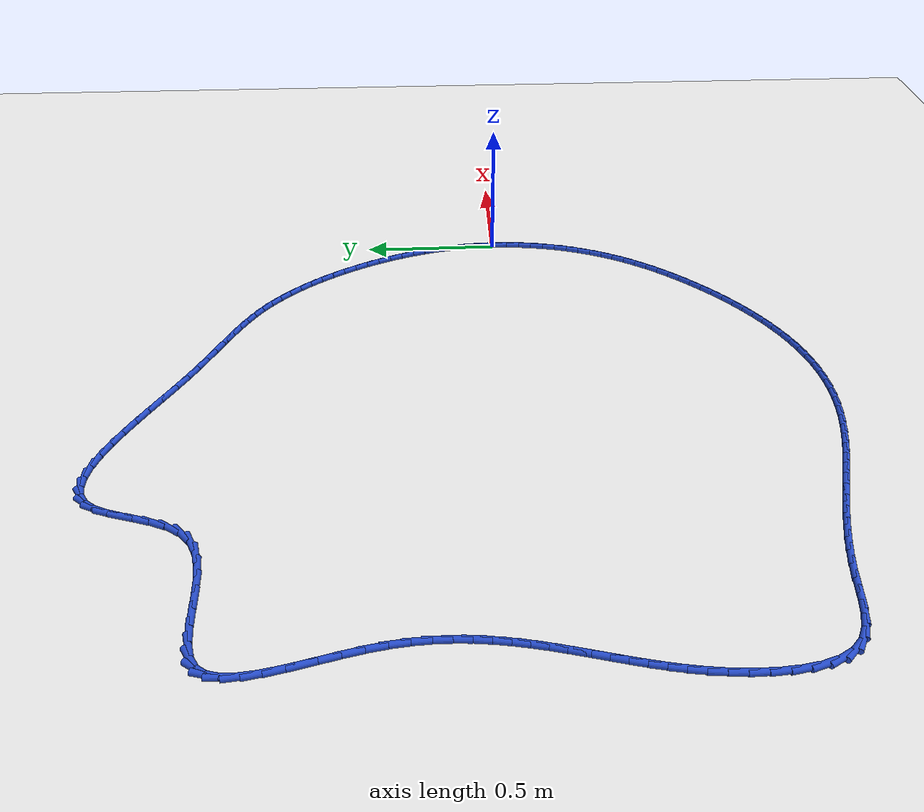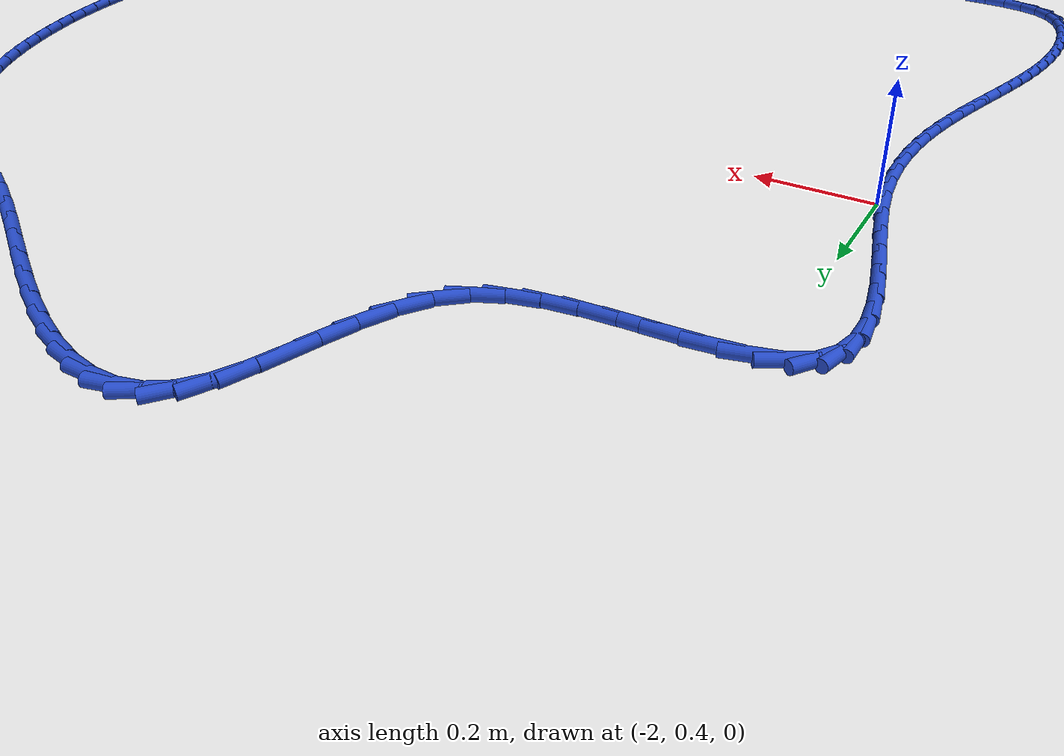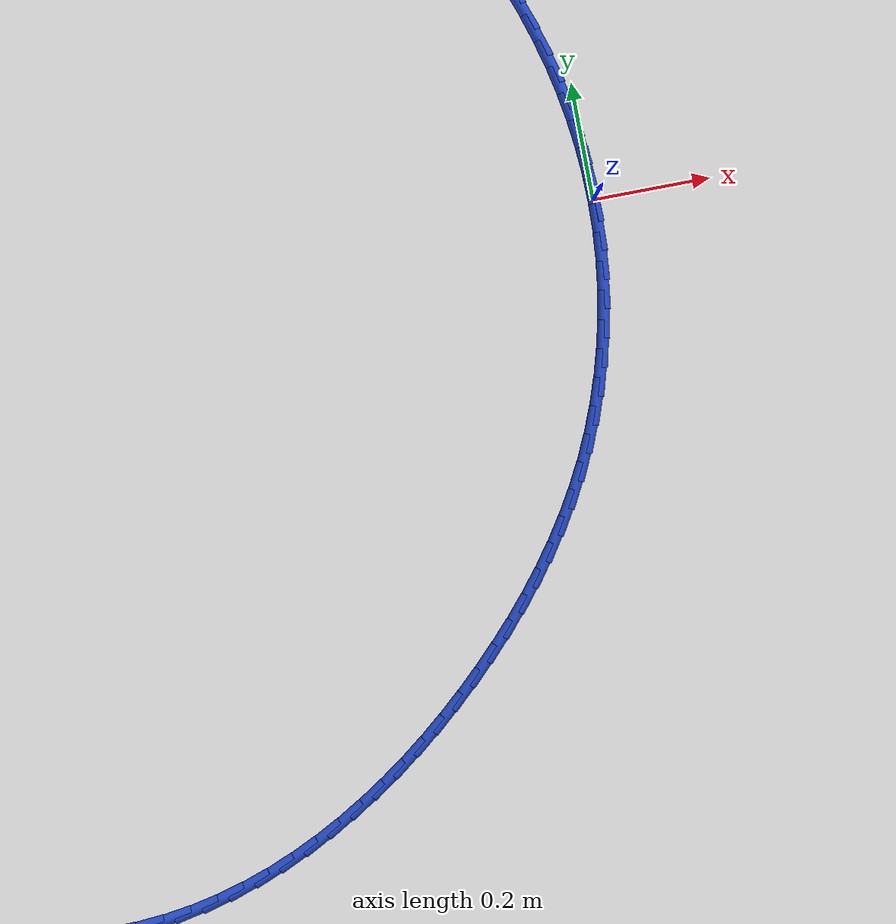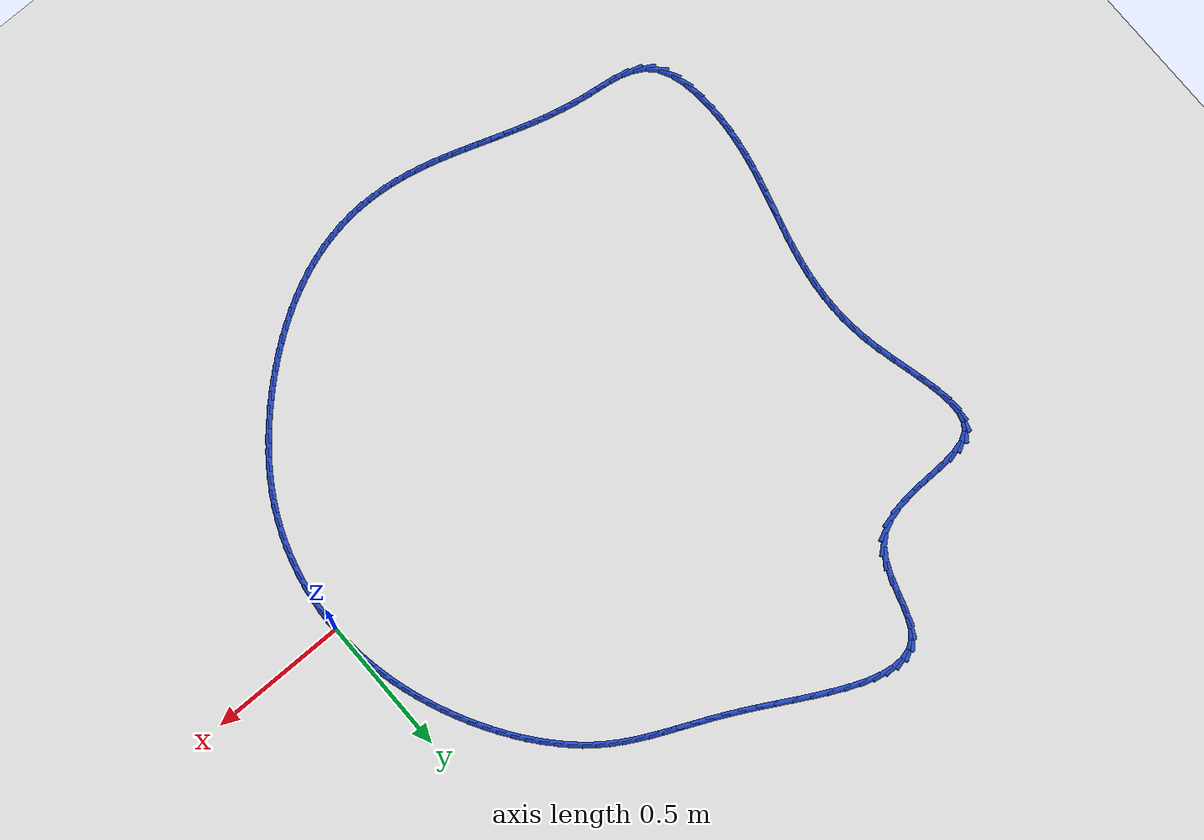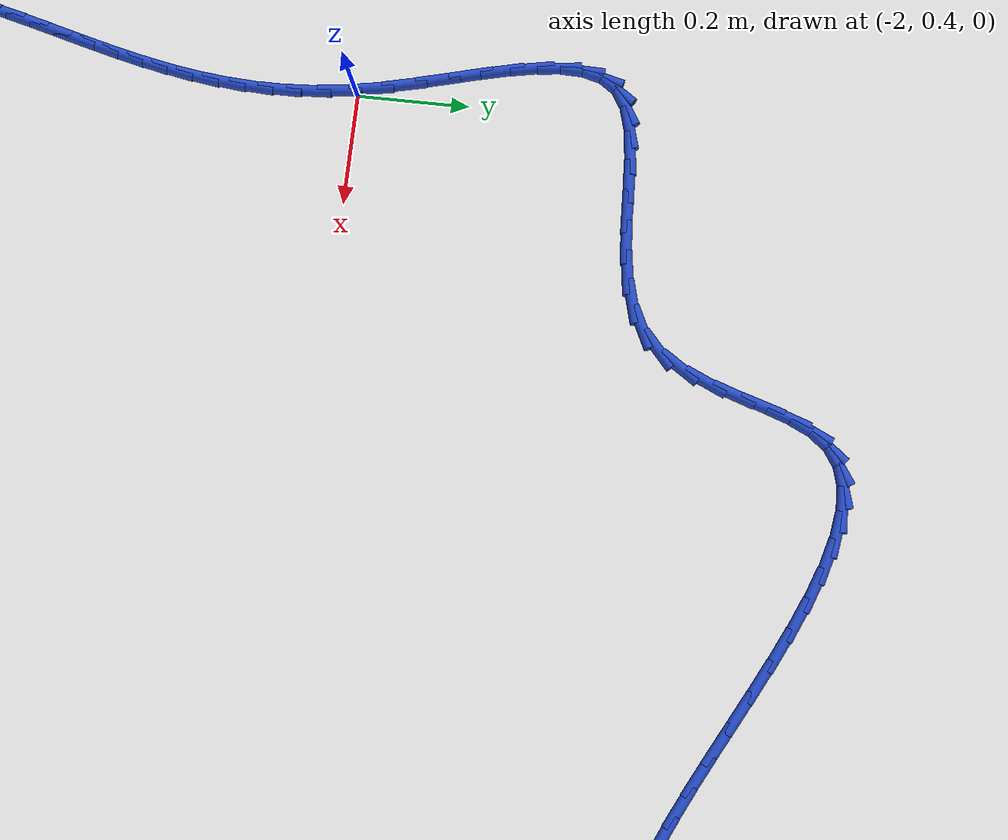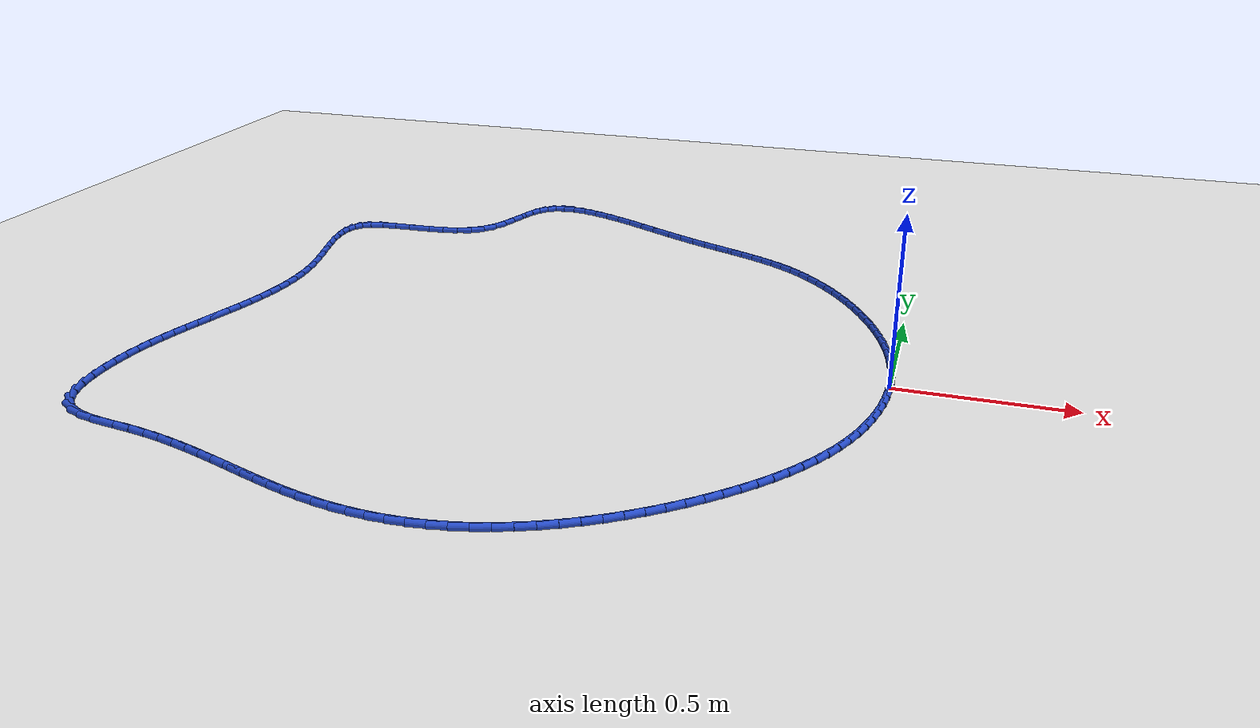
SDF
<sdf version="1.6">
 <world name="default">
  <light name="sun" type="directional">
   <pose>0 0 10 0 -0 0</pose>
   <diffuse>0.8 0.8 0.8 1</diffuse>
   <specular>0.2 0.2 0.2 1</specular>
   <attenuation>
    <range>1000</range>
    <constant>0.9</constant>
    <linear>0.01</linear>
    <quadratic>0.001</quadratic>
   </attenuation>
   <direction>-0.5 0.1 -0.9</direction>
  </light>
  <model name="ground_plane">
   <static>1</static>
   <link name="link">
    <collision name="collision">
     <geometry><plane><normal>0 0 1</normal><size>100 100</size></plane></geometry>
     <surface><friction><ode><mu>100</mu><mu2>50</mu2></ode></friction></surface>
    </collision>
    <visual name="visual">
     <cast_shadows>0</cast_shadows>
     <geometry><plane><normal>0 0 1</normal><size>100 100</size></plane></geometry>
     <material>
      <script><uri>file://media/materials/scripts/gazebo.material</uri><name>Gazebo/WhiteGlow</name></script>
     </material>
    </visual>
   </link>
  </model>
  <gravity>0 0 -9.8</gravity>
  <magnetic_field>6e-06 2.3e-05 -4.2e-05</magnetic_field>
  <atmosphere type="adiabatic"/>
  <physics name="default_physics" default="0" type="ode">
   <max_step_size>0.001</max_step_size>
   <real_time_factor>1</real_time_factor>
   <real_time_update_rate>1000</real_time_update_rate>
  </physics>
  <scene><ambient>0.4 0.4 0.4 1</ambient><background>0.7 0.7 0.7 1</background><shadows>1</shadows></scene>
  <spherical_coordinates>
   <surface_model>EARTH_WGS84</surface_model>
   <latitude_deg>0</latitude_deg>
   <longitude_deg>0</longitude_deg>
   <elevation>0</elevation>
   <heading_deg>0</heading_deg>
  </spherical_coordinates>
  <model name="line">
   <link name="link_0">
    <pose>-1.734723475976807e-18 2.7755575615628914e-17 0.01 0 1.57 -1.5403953769960061</pose>
    <collision name="collision">
     <geometry><cylinder><radius>0.01</radius><length>0.08</length></cylinder></geometry>
    </collision>
    <visual name="visual">
     <material>
      <script><name>Gazebo/Blue</name><uri>file://media/materials/scripts/gazebo.material</uri></script>
     </material>
     <geometry><cylinder><radius>0.01</radius><length>0.08</length></cylinder></geometry>
    </visual>
   </link>
   <link name="link_1">
    <pose>-0.0014700015047816955 0.04833890452229398 0.01 0 1.57 -1.4905525584799248</pose>
    <collision name="collision">
     <geometry><cylinder><radius>0.01</radius><length>0.08</length></cylinder></geometry>
    </collision>
    <visual name="visual">
     <material>
      <script><name>Gazebo/Blue</name><uri>file://media/materials/scripts/gazebo.material</uri></script>
     </material>
     <geometry><cylinder><radius>0.01</radius><length>0.08</length></cylinder></geometry>
    </visual>
   </link>
   <link name="link_2">
    <pose>-0.005338020853893343 0.09643875981137744 0.01 0 1.57 -1.4418619348056134</pose>
    <collision name="collision">
     <geometry><cylinder><radius>0.01</radius><length>0.08</length></cylinder></geometry>
    </collision>
    <visual name="visual">
     <material>
      <script><name>Gazebo/Blue</name><uri>file://media/materials/scripts/gazebo.material</uri></script>
     </material>
     <geometry><cylinder><radius>0.01</radius><length>0.08</length></cylinder></geometry>
    </visual>
   </link>
   <link name="link_3">
    <pose>-0.011541491594309458 0.14428524070696477 0.01 0 1.57 -1.3944919175950468</pose>
    <collision name="collision">
     <geometry><cylinder><radius>0.01</radius><length>0.08</length></cylinder></geometry>
    </collision>
    <visual name="visual">
     <material>
      <script><name>Gazebo/Blue</name><uri>file://media/materials/scripts/gazebo.material</uri></script>
     </material>
     <geometry><cylinder><radius>0.01</radius><length>0.08</length></cylinder></geometry>
    </visual>
   </link>
   <link name="link_4">
    <pose>-0.020017847273004555 0.19186402204877043 0.01 0 1.57 -1.3485784081164802</pose>
    <collision name="collision">
     <geometry><cylinder><radius>0.01</radius><length>0.08</length></cylinder></geometry>
    </collision>
    <visual name="visual">
     <material>
      <script><name>Gazebo/Blue</name><uri>file://media/materials/scripts/gazebo.material</uri></script>
     </material>
     <geometry><cylinder><radius>0.01</radius><length>0.08</length></cylinder></geometry>
    </visual>
   </link>
   <link name="link_5">
    <pose>-0.03070452143695314 0.23916077867650878 0.01 0 1.57 -1.3042248079501102</pose>
    <collision name="collision">
     <geometry><cylinder><radius>0.01</radius><length>0.08</length></cylinder></geometry>
    </collision>
    <visual name="visual">
     <material>
      <script><name>Gazebo/Blue</name><uri>file://media/materials/scripts/gazebo.material</uri></script>
     </material>
     <geometry><cylinder><radius>0.01</radius><length>0.08</length></cylinder></geometry>
    </visual>
   </link>
   <link name="link_6">
    <pose>-0.04353894763312974 0.28616118542989427 0.01 0 1.57 -1.2615034236477323</pose>
    <collision name="collision">
     <geometry><cylinder><radius>0.01</radius><length>0.08</length></cylinder></geometry>
    </collision>
    <visual name="visual">
     <material>
      <script><name>Gazebo/Blue</name><uri>file://media/materials/scripts/gazebo.material</uri></script>
     </material>
     <geometry><cylinder><radius>0.01</radius><length>0.08</length></cylinder></geometry>
    </visual>
   </link>
   <link name="link_7">
    <pose>-0.05845855940850886 0.33285091714864123 0.01 0 1.57 -1.2204579246176617</pose>
    <collision name="collision">
     <geometry><cylinder><radius>0.01</radius><length>0.08</length></cylinder></geometry>
    </collision>
    <visual name="visual">
     <material>
      <script><name>Gazebo/Blue</name><uri>file://media/materials/scripts/gazebo.material</uri></script>
     </material>
     <geometry><cylinder><radius>0.01</radius><length>0.08</length></cylinder></geometry>
    </visual>
   </link>
   <link name="link_8">
    <pose>-0.07540079031006502 0.37921564867246427 0.01 0 1.57 -1.1810928882082674</pose>
    <collision name="collision">
     <geometry><cylinder><radius>0.01</radius><length>0.08</length></cylinder></geometry>
    </collision>
    <visual name="visual">
     <material>
      <script><name>Gazebo/Blue</name><uri>file://media/materials/scripts/gazebo.material</uri></script>
     </material>
     <geometry><cylinder><radius>0.01</radius><length>0.08</length></cylinder></geometry>
    </visual>
   </link>
   <link name="link_9">
    <pose>-0.09430291855344151 0.4252388939659872 0.01 0 1.57 -1.1428250796314008</pose>
    <collision name="collision">
     <geometry><cylinder><radius>0.01</radius><length>0.08</length></cylinder></geometry>
    </collision>
    <visual name="visual">
     <material>
      <script><name>Gazebo/Blue</name><uri>file://media/materials/scripts/gazebo.material</uri></script>
     </material>
     <geometry><cylinder><radius>0.01</radius><length>0.08</length></cylinder></geometry>
    </visual>
   </link>
   <link name="link_10">
    <pose>-0.11509628794032653 0.4708216110330309 0.01 0 1.57 -1.1046605332326702</pose>
    <collision name="collision">
     <geometry><cylinder><radius>0.01</radius><length>0.08</length></cylinder></geometry>
    </collision>
    <visual name="visual">
     <material>
      <script><name>Gazebo/Blue</name><uri>file://media/materials/scripts/gazebo.material</uri></script>
     </material>
     <geometry><cylinder><radius>0.01</radius><length>0.08</length></cylinder></geometry>
    </visual>
   </link>
   <link name="link_11">
    <pose>-0.1377045929425613 0.5157583450488197 0.01 0 1.57 -1.0661541797765959</pose>
    <collision name="collision">
     <geometry><cylinder><radius>0.01</radius><length>0.08</length></cylinder></geometry>
    </collision>
    <visual name="visual">
     <material>
      <script><name>Gazebo/Blue</name><uri>file://media/materials/scripts/gazebo.material</uri></script>
     </material>
     <geometry><cylinder><radius>0.01</radius><length>0.08</length></cylinder></geometry>
    </visual>
   </link>
   <link name="link_12">
    <pose>-0.16205102277417044 0.5598366123488632 0.01 0 1.57 -1.026907348692087</pose>
    <collision name="collision">
     <geometry><cylinder><radius>0.01</radius><length>0.08</length></cylinder></geometry>
    </collision>
    <visual name="visual">
     <material>
      <script><name>Gazebo/Blue</name><uri>file://media/materials/scripts/gazebo.material</uri></script>
     </material>
     <geometry><cylinder><radius>0.01</radius><length>0.08</length></cylinder></geometry>
    </visual>
   </link>
   <link name="link_13">
    <pose>-0.1880587666491787 0.6028439292686713 0.01 0 1.57 -0.9865142577737583</pose>
    <collision name="collision">
     <geometry><cylinder><radius>0.01</radius><length>0.08</length></cylinder></geometry>
    </collision>
    <visual name="visual">
     <material>
      <script><name>Gazebo/Blue</name><uri>file://media/materials/scripts/gazebo.material</uri></script>
     </material>
     <geometry><cylinder><radius>0.01</radius><length>0.08</length></cylinder></geometry>
    </visual>
   </link>
   <link name="link_14">
    <pose>-0.2156510137816109 0.6445678121437545 0.01 0 1.57 -0.9445535184200536</pose>
    <collision name="collision">
     <geometry><cylinder><radius>0.01</radius><length>0.08</length></cylinder></geometry>
    </collision>
    <visual name="visual">
     <material>
      <script><name>Gazebo/Blue</name><uri>file://media/materials/scripts/gazebo.material</uri></script>
     </material>
     <geometry><cylinder><radius>0.01</radius><length>0.08</length></cylinder></geometry>
    </visual>
   </link>
   <link name="link_15">
    <pose>-0.2447509533854917 0.6847957773096223 0.01 0 1.57 -0.9005804672008982</pose>
    <collision name="collision">
     <geometry><cylinder><radius>0.01</radius><length>0.08</length></cylinder></geometry>
    </collision>
    <visual name="visual">
     <material>
      <script><name>Gazebo/Blue</name><uri>file://media/materials/scripts/gazebo.material</uri></script>
     </material>
     <geometry><cylinder><radius>0.01</radius><length>0.08</length></cylinder></geometry>
    </visual>
   </link>
   <link name="link_16">
    <pose>-0.27528177467484577 0.7233153411017847 0.01 0 1.57 -0.8541206822435852</pose>
    <collision name="collision">
     <geometry><cylinder><radius>0.01</radius><length>0.08</length></cylinder></geometry>
    </collision>
    <visual name="visual">
     <material>
      <script><name>Gazebo/Blue</name><uri>file://media/materials/scripts/gazebo.material</uri></script>
     </material>
     <geometry><cylinder><radius>0.01</radius><length>0.08</length></cylinder></geometry>
    </visual>
   </link>
   <link name="link_17">
    <pose>-0.30716666686369803 0.7599140198557524 0.01 0 1.57 -0.8046654321002452</pose>
    <collision name="collision">
     <geometry><cylinder><radius>0.01</radius><length>0.08</length></cylinder></geometry>
    </collision>
    <visual name="visual">
     <material>
      <script><name>Gazebo/Blue</name><uri>file://media/materials/scripts/gazebo.material</uri></script>
     </material>
     <geometry><cylinder><radius>0.01</radius><length>0.08</length></cylinder></geometry>
    </visual>
   </link>
   <link name="link_18">
    <pose>-0.34032881916607305 0.7943793299070345 0.01 0 1.57 -0.7516703677932546</pose>
    <collision name="collision">
     <geometry><cylinder><radius>0.01</radius><length>0.08</length></cylinder></geometry>
    </collision>
    <visual name="visual">
     <material>
      <script><name>Gazebo/Blue</name><uri>file://media/materials/scripts/gazebo.material</uri></script>
     </material>
     <geometry><cylinder><radius>0.01</radius><length>0.08</length></cylinder></geometry>
    </visual>
   </link>
   <link name="link_19">
    <pose>-0.3746914207959958 0.826498787591142 0.01 0 1.57 -0.6945595492141571</pose>
    <collision name="collision">
     <geometry><cylinder><radius>0.01</radius><length>0.08</length></cylinder></geometry>
    </collision>
    <visual name="visual">
     <material>
      <script><name>Gazebo/Blue</name><uri>file://media/materials/scripts/gazebo.material</uri></script>
     </material>
     <geometry><cylinder><radius>0.01</radius><length>0.08</length></cylinder></geometry>
    </visual>
   </link>
   <link name="link_20">
    <pose>-0.41017766096749053 0.8560599092435841 0.01 0 1.57 -0.6330172715650902</pose>
    <collision name="collision">
     <geometry><cylinder><radius>0.01</radius><length>0.08</length></cylinder></geometry>
    </collision>
    <visual name="visual">
     <material>
      <script><name>Gazebo/Blue</name><uri>file://media/materials/scripts/gazebo.material</uri></script>
     </material>
     <geometry><cylinder><radius>0.01</radius><length>0.08</length></cylinder></geometry>
    </visual>
   </link>
   <link name="link_21">
    <pose>-0.44671487801135473 0.882868953788108 0.01 0 1.57 -0.5727634175690438</pose>
    <collision name="collision">
     <geometry><cylinder><radius>0.01</radius><length>0.08</length></cylinder></geometry>
    </collision>
    <visual name="visual">
     <material>
      <script><name>Gazebo/Blue</name><uri>file://media/materials/scripts/gazebo.material</uri></script>
     </material>
     <geometry><cylinder><radius>0.01</radius><length>0.08</length></cylinder></geometry>
    </visual>
   </link>
   <link name="link_22">
    <pose>-0.4843155191185739 0.9071166379522276 0.01 0 1.57 -0.5209109166484821</pose>
    <collision name="collision">
     <geometry><cylinder><radius>0.01</radius><length>0.08</length></cylinder></geometry>
    </collision>
    <visual name="visual">
     <material>
      <script><name>Gazebo/Blue</name><uri>file://media/materials/scripts/gazebo.material</uri></script>
     </material>
     <geometry><cylinder><radius>0.01</radius><length>0.08</length></cylinder></geometry>
    </visual>
   </link>
   <link name="link_23">
    <pose>-0.5230717731653142 0.9293538914082086 0.01 0 1.57 -0.47928181927860614</pose>
    <collision name="collision">
     <geometry><cylinder><radius>0.01</radius><length>0.08</length></cylinder></geometry>
    </collision>
    <visual name="visual">
     <material>
      <script><name>Gazebo/Blue</name><uri>file://media/materials/scripts/gazebo.material</uri></script>
     </material>
     <geometry><cylinder><radius>0.01</radius><length>0.08</length></cylinder></geometry>
    </visual>
   </link>
   <link name="link_24">
    <pose>-0.5630789032815207 0.9501455309941594 0.01 0 1.57 -0.4487235242197466</pose>
    <collision name="collision">
     <geometry><cylinder><radius>0.01</radius><length>0.08</length></cylinder></geometry>
    </collision>
    <visual name="visual">
     <material>
      <script><name>Gazebo/Blue</name><uri>file://media/materials/scripts/gazebo.material</uri></script>
     </material>
     <geometry><cylinder><radius>0.01</radius><length>0.08</length></cylinder></geometry>
    </visual>
   </link>
   <link name="link_25">
    <pose>-0.6044321725971386 0.9700563735481884 0.01 0 1.57 -0.42938831676605915</pose>
    <collision name="collision">
     <geometry><cylinder><radius>0.01</radius><length>0.08</length></cylinder></geometry>
    </collision>
    <visual name="visual">
     <material>
      <script><name>Gazebo/Blue</name><uri>file://media/materials/scripts/gazebo.material</uri></script>
     </material>
     <geometry><cylinder><radius>0.01</radius><length>0.08</length></cylinder></geometry>
    </visual>
   </link>
   <link name="link_26">
    <pose>-0.6472268442421124 0.9896512359084035 0.01 0 1.57 -0.42087494429750116</pose>
    <collision name="collision">
     <geometry><cylinder><radius>0.01</radius><length>0.08</length></cylinder></geometry>
    </collision>
    <visual name="visual">
     <material>
      <script><name>Gazebo/Blue</name><uri>file://media/materials/scripts/gazebo.material</uri></script>
     </material>
     <geometry><cylinder><radius>0.01</radius><length>0.08</length></cylinder></geometry>
    </visual>
   </link>
   <link name="link_27">
    <pose>-0.6915581813463882 1.0094949349129139 0.01 0 1.57 -0.42238129655033674</pose>
    <collision name="collision">
     <geometry><cylinder><radius>0.01</radius><length>0.08</length></cylinder></geometry>
    </collision>
    <visual name="visual">
     <material>
      <script><name>Gazebo/Blue</name><uri>file://media/materials/scripts/gazebo.material</uri></script>
     </material>
     <geometry><cylinder><radius>0.01</radius><length>0.08</length></cylinder></geometry>
    </visual>
   </link>
   <link name="link_28">
    <pose>-0.7375214470399101 1.0301522873998266 0.01 0 1.57 -0.43283712403460456</pose>
    <collision name="collision">
     <geometry><cylinder><radius>0.01</radius><length>0.08</length></cylinder></geometry>
    </collision>
    <visual name="visual">
     <material>
      <script><name>Gazebo/Blue</name><uri>file://media/materials/scripts/gazebo.material</uri></script>
     </material>
     <geometry><cylinder><radius>0.01</radius><length>0.08</length></cylinder></geometry>
    </visual>
   </link>
   <link name="link_29">
    <pose>-0.7852119044526238 1.052188110207251 0.01 0 1.57 -0.4510090140028726</pose>
    <collision name="collision">
     <geometry><cylinder><radius>0.01</radius><length>0.08</length></cylinder></geometry>
    </collision>
    <visual name="visual">
     <material>
      <script><name>Gazebo/Blue</name><uri>file://media/materials/scripts/gazebo.material</uri></script>
     </material>
     <geometry><cylinder><radius>0.01</radius><length>0.08</length></cylinder></geometry>
    </visual>
   </link>
   <link name="link_30">
    <pose>-0.8347248167144743 1.0761672201732948 0.01 0 1.57 -0.47500331755660985</pose>
    <collision name="collision">
     <geometry><cylinder><radius>0.01</radius><length>0.08</length></cylinder></geometry>
    </collision>
    <visual name="visual">
     <material>
      <script><name>Gazebo/Blue</name><uri>file://media/materials/scripts/gazebo.material</uri></script>
     </material>
     <geometry><cylinder><radius>0.01</radius><length>0.08</length></cylinder></geometry>
    </visual>
   </link>
   <link name="link_31">
    <pose>-0.8861343882812149 1.1026059448422485 0.01 0 1.57 -0.4942131199377108</pose>
    <collision name="collision">
     <geometry><cylinder><radius>0.01</radius><length>0.08</length></cylinder></geometry>
    </collision>
    <visual name="visual">
     <material>
      <script><name>Gazebo/Blue</name><uri>file://media/materials/scripts/gazebo.material</uri></script>
     </material>
     <geometry><cylinder><radius>0.01</radius><length>0.08</length></cylinder></geometry>
    </visual>
   </link>
   <link name="link_32">
    <pose>-0.939144797298409 1.1311685963697733 0.01 0 1.57 -0.5017601034455197</pose>
    <collision name="collision">
     <geometry><cylinder><radius>0.01</radius><length>0.08</length></cylinder></geometry>
    </collision>
    <visual name="visual">
     <material>
      <script><name>Gazebo/Blue</name><uri>file://media/materials/scripts/gazebo.material</uri></script>
     </material>
     <geometry><cylinder><radius>0.01</radius><length>0.08</length></cylinder></geometry>
    </visual>
   </link>
   <link name="link_33">
    <pose>-0.9931443782543097 1.1607922314461274 0.01 0 1.57 -0.498547334348503</pose>
    <collision name="collision">
     <geometry><cylinder><radius>0.01</radius><length>0.08</length></cylinder></geometry>
    </collision>
    <visual name="visual">
     <material>
      <script><name>Gazebo/Blue</name><uri>file://media/materials/scripts/gazebo.material</uri></script>
     </material>
     <geometry><cylinder><radius>0.01</radius><length>0.08</length></cylinder></geometry>
    </visual>
   </link>
   <link name="link_34">
    <pose>-1.0475113287188682 1.1903905656905476 0.01 0 1.57 -0.4845716500360975</pose>
    <collision name="collision">
     <geometry><cylinder><radius>0.01</radius><length>0.08</length></cylinder></geometry>
    </collision>
    <visual name="visual">
     <material>
      <script><name>Gazebo/Blue</name><uri>file://media/materials/scripts/gazebo.material</uri></script>
     </material>
     <geometry><cylinder><radius>0.01</radius><length>0.08</length></cylinder></geometry>
    </visual>
   </link>
   <link name="link_35">
    <pose>-1.101623846262037 1.2188773147222722 0.01 0 1.57 -0.45868744966806807</pose>
    <collision name="collision">
     <geometry><cylinder><radius>0.01</radius><length>0.08</length></cylinder></geometry>
    </collision>
    <visual name="visual">
     <material>
      <script><name>Gazebo/Blue</name><uri>file://media/materials/scripts/gazebo.material</uri></script>
     </material>
     <geometry><cylinder><radius>0.01</radius><length>0.08</length></cylinder></geometry>
    </visual>
   </link>
   <link name="link_36">
    <pose>-1.1548601284537683 1.2451661941605388 0.01 0 1.57 -0.4183849131545252</pose>
    <collision name="collision">
     <geometry><cylinder><radius>0.01</radius><length>0.08</length></cylinder></geometry>
    </collision>
    <visual name="visual">
     <material>
      <script><name>Gazebo/Blue</name><uri>file://media/materials/scripts/gazebo.material</uri></script>
     </material>
     <geometry><cylinder><radius>0.01</radius><length>0.08</length></cylinder></geometry>
    </visual>
   </link>
   <link name="link_37">
    <pose>-1.206598372864014 1.2681709196245843 0.01 0 1.57 -0.3592544600759173</pose>
    <collision name="collision">
     <geometry><cylinder><radius>0.01</radius><length>0.08</length></cylinder></geometry>
    </collision>
    <visual name="visual">
     <material>
      <script><name>Gazebo/Blue</name><uri>file://media/materials/scripts/gazebo.material</uri></script>
     </material>
     <geometry><cylinder><radius>0.01</radius><length>0.08</length></cylinder></geometry>
    </visual>
   </link>
   <link name="link_38">
    <pose>-1.256216777062726 1.2868052067336466 0.01 0 1.57 -0.2740384587538279</pose>
    <collision name="collision">
     <geometry><cylinder><radius>0.01</radius><length>0.08</length></cylinder></geometry>
    </collision>
    <visual name="visual">
     <material>
      <script><name>Gazebo/Blue</name><uri>file://media/materials/scripts/gazebo.material</uri></script>
     </material>
     <geometry><cylinder><radius>0.01</radius><length>0.08</length></cylinder></geometry>
    </visual>
   </link>
   <link name="link_39">
    <pose>-1.303093538619856 1.2999827711069638 0.01 0 1.57 -0.15130655509844626</pose>
    <collision name="collision">
     <geometry><cylinder><radius>0.01</radius><length>0.08</length></cylinder></geometry>
    </collision>
    <visual name="visual">
     <material>
      <script><name>Gazebo/Blue</name><uri>file://media/materials/scripts/gazebo.material</uri></script>
     </material>
     <geometry><cylinder><radius>0.01</radius><length>0.08</length></cylinder></geometry>
    </visual>
   </link>
   <link name="link_40">
    <pose>-1.346606855105357 1.3066173283637725 0.01 0 1.57 0.025159952422445273</pose>
    <collision name="collision">
     <geometry><cylinder><radius>0.01</radius><length>0.08</length></cylinder></geometry>
    </collision>
    <visual name="visual">
     <material>
      <script><name>Gazebo/Blue</name><uri>file://media/materials/scripts/gazebo.material</uri></script>
     </material>
     <geometry><cylinder><radius>0.01</radius><length>0.08</length></cylinder></geometry>
    </visual>
   </link>
   <link name="link_41">
    <pose>-1.38613492408918 1.3056225941233106 0.01 0 1.57 0.27121339722972543</pose>
    <collision name="collision">
     <geometry><cylinder><radius>0.01</radius><length>0.08</length></cylinder></geometry>
    </collision>
    <visual name="visual">
     <material>
      <script><name>Gazebo/Blue</name><uri>file://media/materials/scripts/gazebo.material</uri></script>
     </material>
     <geometry><cylinder><radius>0.01</radius><length>0.08</length></cylinder></geometry>
    </visual>
   </link>
   <link name="link_42">
    <pose>-1.421055943141278 1.2959122840048165 0.01 0 1.57 0.5813843029608146</pose>
    <collision name="collision">
     <geometry><cylinder><radius>0.01</radius><length>0.08</length></cylinder></geometry>
    </collision>
    <visual name="visual">
     <material>
      <script><name>Gazebo/Blue</name><uri>file://media/materials/scripts/gazebo.material</uri></script>
     </material>
     <geometry><cylinder><radius>0.01</radius><length>0.08</length></cylinder></geometry>
    </visual>
   </link>
   <link name="link_43">
    <pose>-1.450748109831602 1.2764001136275265 0.01 0 1.57 0.9028113712699611</pose>
    <collision name="collision">
     <geometry><cylinder><radius>0.01</radius><length>0.08</length></cylinder></geometry>
    </collision>
    <visual name="visual">
     <material>
      <script><name>Gazebo/Blue</name><uri>file://media/materials/scripts/gazebo.material</uri></script>
     </material>
     <geometry><cylinder><radius>0.01</radius><length>0.08</length></cylinder></geometry>
    </visual>
   </link>
   <link name="link_44">
    <pose>-1.4746551207610308 1.2460989352192935 0.01 0 1.57 1.1278436671565717</pose>
    <collision name="collision">
     <geometry><cylinder><radius>0.01</radius><length>0.08</length></cylinder></geometry>
    </collision>
    <visual name="visual">
     <material>
      <script><name>Gazebo/Blue</name><uri>file://media/materials/scripts/gazebo.material</uri></script>
     </material>
     <geometry><cylinder><radius>0.01</radius><length>0.08</length></cylinder></geometry>
    </visual>
   </link>
   <link name="link_45">
    <pose>-1.4936150824372239 1.2061321218389334 0.01 0 1.57 1.2357545950595765</pose>
    <collision name="collision">
     <geometry><cylinder><radius>0.01</radius><length>0.08</length></cylinder></geometry>
    </collision>
    <visual name="visual">
     <material>
      <script><name>Gazebo/Blue</name><uri>file://media/materials/scripts/gazebo.material</uri></script>
     </material>
     <geometry><cylinder><radius>0.01</radius><length>0.08</length></cylinder></geometry>
    </visual>
   </link>
   <link name="link_46">
    <pose>-1.5098009546337579 1.159643424922019 0.01 0 1.57 1.2664430498191577</pose>
    <collision name="collision">
     <geometry><cylinder><radius>0.01</radius><length>0.08</length></cylinder></geometry>
    </collision>
    <visual name="visual">
     <material>
      <script><name>Gazebo/Blue</name><uri>file://media/materials/scripts/gazebo.material</uri></script>
     </material>
     <geometry><cylinder><radius>0.01</radius><length>0.08</length></cylinder></geometry>
    </visual>
   </link>
   <link name="link_47">
    <pose>-1.5254392777120986 1.1098576932531345 0.01 0 1.57 1.2364991724893934</pose>
    <collision name="collision">
     <geometry><cylinder><radius>0.01</radius><length>0.08</length></cylinder></geometry>
    </collision>
    <visual name="visual">
     <material>
      <script><name>Gazebo/Blue</name><uri>file://media/materials/scripts/gazebo.material</uri></script>
     </material>
     <geometry><cylinder><radius>0.01</radius><length>0.08</length></cylinder></geometry>
    </visual>
   </link>
   <link name="link_48">
    <pose>-1.5427565920337118 1.0599997756168642 0.01 0 1.57 1.1442897762193545</pose>
    <collision name="collision">
     <geometry><cylinder><radius>0.01</radius><length>0.08</length></cylinder></geometry>
    </collision>
    <visual name="visual">
     <material>
      <script><name>Gazebo/Blue</name><uri>file://media/materials/scripts/gazebo.material</uri></script>
     </material>
     <geometry><cylinder><radius>0.01</radius><length>0.08</length></cylinder></geometry>
    </visual>
   </link>
   <link name="link_49">
    <pose>-1.5639794379600636 1.0132945207977917 0.01 0 1.57 0.9747727064990936</pose>
    <collision name="collision">
     <geometry><cylinder><radius>0.01</radius><length>0.08</length></cylinder></geometry>
    </collision>
    <visual name="visual">
     <material>
      <script><name>Gazebo/Blue</name><uri>file://media/materials/scripts/gazebo.material</uri></script>
     </material>
     <geometry><cylinder><radius>0.01</radius><length>0.08</length></cylinder></geometry>
    </visual>
   </link>
   <link name="link_50">
    <pose>-1.5913343558526196 0.9729667775805014 0.01 0 1.57 0.7133617323919044</pose>
    <collision name="collision">
     <geometry><cylinder><radius>0.01</radius><length>0.08</length></cylinder></geometry>
    </collision>
    <visual name="visual">
     <material>
      <script><name>Gazebo/Blue</name><uri>file://media/materials/scripts/gazebo.material</uri></script>
     </material>
     <geometry><cylinder><radius>0.01</radius><length>0.08</length></cylinder></geometry>
    </visual>
   </link>
   <link name="link_51">
    <pose>-1.6269608597573857 0.9421359227537957 0.01 0 1.57 0.44175981498868566</pose>
    <collision name="collision">
     <geometry><cylinder><radius>0.01</radius><length>0.08</length></cylinder></geometry>
    </collision>
    <visual name="visual">
     <material>
      <script><name>Gazebo/Blue</name><uri>file://media/materials/scripts/gazebo.material</uri></script>
     </material>
     <geometry><cylinder><radius>0.01</radius><length>0.08</length></cylinder></geometry>
    </visual>
   </link>
   <link name="link_52">
    <pose>-1.6708867059713308 0.9213619773159422 0.01 0 1.57 0.25010813463742065</pose>
    <collision name="collision">
     <geometry><cylinder><radius>0.01</radius><length>0.08</length></cylinder></geometry>
    </collision>
    <visual name="visual">
     <material>
      <script><name>Gazebo/Blue</name><uri>file://media/materials/scripts/gazebo.material</uri></script>
     </material>
     <geometry><cylinder><radius>0.01</radius><length>0.08</length></cylinder></geometry>
    </visual>
   </link>
   <link name="link_53">
    <pose>-1.7209648215612499 0.9085691666649782 0.01 0 1.57 0.12909898963427596</pose>
    <collision name="collision">
     <geometry><cylinder><radius>0.01</radius><length>0.08</length></cylinder></geometry>
    </collision>
    <visual name="visual">
     <material>
      <script><name>Gazebo/Blue</name><uri>file://media/materials/scripts/gazebo.material</uri></script>
     </material>
     <geometry><cylinder><radius>0.01</radius><length>0.08</length></cylinder></geometry>
    </visual>
   </link>
   <link name="link_54">
    <pose>-1.7749484895573153 0.9015609520903517 0.01 0 1.57 0.061389395709760784</pose>
    <collision name="collision">
     <geometry><cylinder><radius>0.01</radius><length>0.08</length></cylinder></geometry>
    </collision>
    <visual name="visual">
     <material>
      <script><name>Gazebo/Blue</name><uri>file://media/materials/scripts/gazebo.material</uri></script>
     </material>
     <geometry><cylinder><radius>0.01</radius><length>0.08</length></cylinder></geometry>
    </visual>
   </link>
   <link name="link_55">
    <pose>-1.8305909929896986 0.8981407948815096 0.01 0 1.57 0.03683107973037563</pose>
    <collision name="collision">
     <geometry><cylinder><radius>0.01</radius><length>0.08</length></cylinder></geometry>
    </collision>
    <visual name="visual">
     <material>
      <script><name>Gazebo/Blue</name><uri>file://media/materials/scripts/gazebo.material</uri></script>
     </material>
     <geometry><cylinder><radius>0.01</radius><length>0.08</length></cylinder></geometry>
    </visual>
   </link>
   <link name="link_56">
    <pose>-1.885645614888574 0.8961121563278991 0.01 0 1.57 0.05421066541980383</pose>
    <collision name="collision">
     <geometry><cylinder><radius>0.01</radius><length>0.08</length></cylinder></geometry>
    </collision>
    <visual name="visual">
     <material>
      <script><name>Gazebo/Blue</name><uri>file://media/materials/scripts/gazebo.material</uri></script>
     </material>
     <geometry><cylinder><radius>0.01</radius><length>0.08</length></cylinder></geometry>
    </visual>
   </link>
   <link name="link_57">
    <pose>-1.9378656382841117 0.8932784977189667 0.01 0 1.57 0.12316169303003952</pose>
    <collision name="collision">
     <geometry><cylinder><radius>0.01</radius><length>0.08</length></cylinder></geometry>
    </collision>
    <visual name="visual">
     <material>
      <script><name>Gazebo/Blue</name><uri>file://media/materials/scripts/gazebo.material</uri></script>
     </material>
     <geometry><cylinder><radius>0.01</radius><length>0.08</length></cylinder></geometry>
    </visual>
   </link>
   <link name="link_58">
    <pose>-1.9850043462064861 0.8874432803441609 0.01 0 1.57 0.2703589593264915</pose>
    <collision name="collision">
     <geometry><cylinder><radius>0.01</radius><length>0.08</length></cylinder></geometry>
    </collision>
    <visual name="visual">
     <material>
      <script><name>Gazebo/Blue</name><uri>file://media/materials/scripts/gazebo.material</uri></script>
     </material>
     <geometry><cylinder><radius>0.01</radius><length>0.08</length></cylinder></geometry>
    </visual>
   </link>
   <link name="link_59">
    <pose>-2.024815021685868 0.8764099654929276 0.01 0 1.57 0.5473379196692671</pose>
    <collision name="collision">
     <geometry><cylinder><radius>0.01</radius><length>0.08</length></cylinder></geometry>
    </collision>
    <visual name="visual">
     <material>
      <script><name>Gazebo/Blue</name><uri>file://media/materials/scripts/gazebo.material</uri></script>
     </material>
     <geometry><cylinder><radius>0.01</radius><length>0.08</length></cylinder></geometry>
    </visual>
   </link>
   <link name="link_60">
    <pose>-2.055051428395079 0.8579824351364899 0.01 0 1.57 0.9561282580025697</pose>
    <collision name="collision">
     <geometry><cylinder><radius>0.01</radius><length>0.08</length></cylinder></geometry>
    </collision>
    <visual name="visual">
     <material>
      <script><name>Gazebo/Blue</name><uri>file://media/materials/scripts/gazebo.material</uri></script>
     </material>
     <geometry><cylinder><radius>0.01</radius><length>0.08</length></cylinder></geometry>
    </visual>
   </link>
   <link name="link_61">
    <pose>-2.0743089694504455 0.8307012149385453 0.01 0 1.57 1.309626006054948</pose>
    <collision name="collision">
     <geometry><cylinder><radius>0.01</radius><length>0.08</length></cylinder></geometry>
    </collision>
    <visual name="visual">
     <material>
      <script><name>Gazebo/Blue</name><uri>file://media/materials/scripts/gazebo.material</uri></script>
     </material>
     <geometry><cylinder><radius>0.01</radius><length>0.08</length></cylinder></geometry>
    </visual>
   </link>
   <link name="link_62">
    <pose>-2.08375528293967 0.7953581754609503 0.01 0 1.57 1.5401687017596222</pose>
    <collision name="collision">
     <geometry><cylinder><radius>0.01</radius><length>0.08</length></cylinder></geometry>
    </collision>
    <visual name="visual">
     <material>
      <script><name>Gazebo/Blue</name><uri>file://media/materials/scripts/gazebo.material</uri></script>
     </material>
     <geometry><cylinder><radius>0.01</radius><length>0.08</length></cylinder></geometry>
    </visual>
   </link>
   <link name="link_63">
    <pose>-2.085047694750176 0.7531737857963612 0.01 0 1.57 -1.462361610571226</pose>
    <collision name="collision">
     <geometry><cylinder><radius>0.01</radius><length>0.08</length></cylinder></geometry>
    </collision>
    <visual name="visual">
     <material>
      <script><name>Gazebo/Blue</name><uri>file://media/materials/scripts/gazebo.material</uri></script>
     </material>
     <geometry><cylinder><radius>0.01</radius><length>0.08</length></cylinder></geometry>
    </visual>
   </link>
   <link name="link_64">
    <pose>-2.079843530769392 0.7053685150374346 0.01 0 1.57 -1.3807367475252352</pose>
    <collision name="collision">
     <geometry><cylinder><radius>0.01</radius><length>0.08</length></cylinder></geometry>
    </collision>
    <visual name="visual">
     <material>
      <script><name>Gazebo/Blue</name><uri>file://media/materials/scripts/gazebo.material</uri></script>
     </material>
     <geometry><cylinder><radius>0.01</radius><length>0.08</length></cylinder></geometry>
    </visual>
   </link>
   <link name="link_65">
    <pose>-2.0698001168847435 0.6531628322768265 0.01 0 1.57 -1.3363991016524521</pose>
    <collision name="collision">
     <geometry><cylinder><radius>0.01</radius><length>0.08</length></cylinder></geometry>
    </collision>
    <visual name="visual">
     <material>
      <script><name>Gazebo/Blue</name><uri>file://media/materials/scripts/gazebo.material</uri></script>
     </material>
     <geometry><cylinder><radius>0.01</radius><length>0.08</length></cylinder></geometry>
    </visual>
   </link>
   <link name="link_66">
    <pose>-2.0565747789836566 0.5977772066071935 0.01 0 1.57 -1.319040057331741</pose>
    <collision name="collision">
     <geometry><cylinder><radius>0.01</radius><length>0.08</length></cylinder></geometry>
    </collision>
    <visual name="visual">
     <material>
      <script><name>Gazebo/Blue</name><uri>file://media/materials/scripts/gazebo.material</uri></script>
     </material>
     <geometry><cylinder><radius>0.01</radius><length>0.08</length></cylinder></geometry>
    </visual>
   </link>
   <link name="link_67">
    <pose>-2.041824842953558 0.5404321071211909 0.01 0 1.57 -1.324259765639215</pose>
    <collision name="collision">
     <geometry><cylinder><radius>0.01</radius><length>0.08</length></cylinder></geometry>
    </collision>
    <visual name="visual">
     <material>
      <script><name>Gazebo/Blue</name><uri>file://media/materials/scripts/gazebo.material</uri></script>
     </material>
     <geometry><cylinder><radius>0.01</radius><length>0.08</length></cylinder></geometry>
    </visual>
   </link>
   <link name="link_68">
    <pose>-2.0272076346818744 0.4823480029114765 0.01 0 1.57 -1.3516878999902016</pose>
    <collision name="collision">
     <geometry><cylinder><radius>0.01</radius><length>0.08</length></cylinder></geometry>
    </collision>
    <visual name="visual">
     <material>
      <script><name>Gazebo/Blue</name><uri>file://media/materials/scripts/gazebo.material</uri></script>
     </material>
     <geometry><cylinder><radius>0.01</radius><length>0.08</length></cylinder></geometry>
    </visual>
   </link>
   <link name="link_69">
    <pose>-2.014380480056032 0.42474536307070604 0.01 0 1.57 -1.4028089462743119</pose>
    <collision name="collision">
     <geometry><cylinder><radius>0.01</radius><length>0.08</length></cylinder></geometry>
    </collision>
    <visual name="visual">
     <material>
      <script><name>Gazebo/Blue</name><uri>file://media/materials/scripts/gazebo.material</uri></script>
     </material>
     <geometry><cylinder><radius>0.01</radius><length>0.08</length></cylinder></geometry>
    </visual>
   </link>
   <link name="link_70">
    <pose>-2.004887013682652 0.3687649866076289 0.01 0 1.57 -1.4639432106400057</pose>
    <collision name="collision">
     <geometry><cylinder><radius>0.01</radius><length>0.08</length></cylinder></geometry>
    </collision>
    <visual name="visual">
     <material>
      <script><name>Gazebo/Blue</name><uri>file://media/materials/scripts/gazebo.material</uri></script>
     </material>
     <geometry><cylinder><radius>0.01</radius><length>0.08</length></cylinder></geometry>
    </visual>
   </link>
   <link name="link_71">
    <pose>-1.9990900835492122 0.3147202267641924 0.01 0 1.57 -1.5242138840212</pose>
    <collision name="collision">
     <geometry><cylinder><radius>0.01</radius><length>0.08</length></cylinder></geometry>
    </collision>
    <visual name="visual">
     <material>
      <script><name>Gazebo/Blue</name><uri>file://media/materials/scripts/gazebo.material</uri></script>
     </material>
     <geometry><cylinder><radius>0.01</radius><length>0.08</length></cylinder></geometry>
    </visual>
   </link>
   <link name="link_72">
    <pose>-1.9966527011130464 0.2624340206775812 0.01 0 1.57 1.5594382615160245</pose>
    <collision name="collision">
     <geometry><cylinder><radius>0.01</radius><length>0.08</length></cylinder></geometry>
    </collision>
    <visual name="visual">
     <material>
      <script><name>Gazebo/Blue</name><uri>file://media/materials/scripts/gazebo.material</uri></script>
     </material>
     <geometry><cylinder><radius>0.01</radius><length>0.08</length></cylinder></geometry>
    </visual>
   </link>
   <link name="link_73">
    <pose>-1.9972287063458751 0.21172287849230825 0.01 0 1.57 1.505131314645567</pose>
    <collision name="collision">
     <geometry><cylinder><radius>0.01</radius><length>0.08</length></cylinder></geometry>
    </collision>
    <visual name="visual">
     <material>
      <script><name>Gazebo/Blue</name><uri>file://media/materials/scripts/gazebo.material</uri></script>
     </material>
     <geometry><cylinder><radius>0.01</radius><length>0.08</length></cylinder></geometry>
    </visual>
   </link>
   <link name="link_74">
    <pose>-2.0004719392194197 0.1624033103528871 0.01 0 1.57 1.4556535782360034</pose>
    <collision name="collision">
     <geometry><cylinder><radius>0.01</radius><length>0.08</length></cylinder></geometry>
    </collision>
    <visual name="visual">
     <material>
      <script><name>Gazebo/Blue</name><uri>file://media/materials/scripts/gazebo.material</uri></script>
     </material>
     <geometry><cylinder><radius>0.01</radius><length>0.08</length></cylinder></geometry>
    </visual>
   </link>
   <link name="link_75">
    <pose>-2.0060362397054 0.11429182640383104 0.01 0 1.57 1.4120311995359334</pose>
    <collision name="collision">
     <geometry><cylinder><radius>0.01</radius><length>0.08</length></cylinder></geometry>
    </collision>
    <visual name="visual">
     <material>
      <script><name>Gazebo/Blue</name><uri>file://media/materials/scripts/gazebo.material</uri></script>
     </material>
     <geometry><cylinder><radius>0.01</radius><length>0.08</length></cylinder></geometry>
    </visual>
   </link>
   <link name="link_76">
    <pose>-2.0135754477755365 0.06720493678965321 0.01 0 1.57 1.3750896683005083</pose>
    <collision name="collision">
     <geometry><cylinder><radius>0.01</radius><length>0.08</length></cylinder></geometry>
    </collision>
    <visual name="visual">
     <material>
      <script><name>Gazebo/Blue</name><uri>file://media/materials/scripts/gazebo.material</uri></script>
     </material>
     <geometry><cylinder><radius>0.01</radius><length>0.08</length></cylinder></geometry>
    </visual>
   </link>
   <link name="link_77">
    <pose>-2.022743403401551 0.020959151654867374 0.01 0 1.57 1.3454517303889237</pose>
    <collision name="collision">
     <geometry><cylinder><radius>0.01</radius><length>0.08</length></cylinder></geometry>
    </collision>
    <visual name="visual">
     <material>
      <script><name>Gazebo/Blue</name><uri>file://media/materials/scripts/gazebo.material</uri></script>
     </material>
     <geometry><cylinder><radius>0.01</radius><length>0.08</length></cylinder></geometry>
    </visual>
   </link>
   <link name="link_78">
    <pose>-2.033193946555162 -0.024629018856012173 0.01 0 1.57 1.3235562531275824</pose>
    <collision name="collision">
     <geometry><cylinder><radius>0.01</radius><length>0.08</length></cylinder></geometry>
    </collision>
    <visual name="visual">
     <material>
      <script><name>Gazebo/Blue</name><uri>file://media/materials/scripts/gazebo.material</uri></script>
     </material>
     <geometry><cylinder><radius>0.01</radius><length>0.08</length></cylinder></geometry>
    </visual>
   </link>
   <link name="link_79">
    <pose>-2.0445809172080924 -0.06974306459847367 0.01 0 1.57 1.3096872729367188</pose>
    <collision name="collision">
     <geometry><cylinder><radius>0.01</radius><length>0.08</length></cylinder></geometry>
    </collision>
    <visual name="visual">
     <material>
      <script><name>Gazebo/Blue</name><uri>file://media/materials/scripts/gazebo.material</uri></script>
     </material>
     <geometry><cylinder><radius>0.01</radius><length>0.08</length></cylinder></geometry>
    </visual>
   </link>
   <link name="link_80">
    <pose>-2.056558155332061 -0.11456647542800209 0.01 0 1.57 1.3040031600596171</pose>
    <collision name="collision">
     <geometry><cylinder><radius>0.01</radius><length>0.08</length></cylinder></geometry>
    </collision>
    <visual name="visual">
     <material>
      <script><name>Gazebo/Blue</name><uri>file://media/materials/scripts/gazebo.material</uri></script>
     </material>
     <geometry><cylinder><radius>0.01</radius><length>0.08</length></cylinder></geometry>
    </visual>
   </link>
   <link name="link_81">
    <pose>-2.0687795008987893 -0.15928274120008554 0.01 0 1.57 1.3065583668813472</pose>
    <collision name="collision">
     <geometry><cylinder><radius>0.01</radius><length>0.08</length></cylinder></geometry>
    </collision>
    <visual name="visual">
     <material>
      <script><name>Gazebo/Blue</name><uri>file://media/materials/scripts/gazebo.material</uri></script>
     </material>
     <geometry><cylinder><radius>0.01</radius><length>0.08</length></cylinder></geometry>
    </visual>
   </link>
   <link name="link_82">
    <pose>-2.0808987938799985 -0.2040753517702099 0.01 0 1.57 1.3173132360086597</pose>
    <collision name="collision">
     <geometry><cylinder><radius>0.01</radius><length>0.08</length></cylinder></geometry>
    </collision>
    <visual name="visual">
     <material>
      <script><name>Gazebo/Blue</name><uri>file://media/materials/scripts/gazebo.material</uri></script>
     </material>
     <geometry><cylinder><radius>0.01</radius><length>0.08</length></cylinder></geometry>
    </visual>
   </link>
   <link name="link_83">
    <pose>-2.0925698742474075 -0.2491277969938609 0.01 0 1.57 1.3361301728690023</pose>
    <collision name="collision">
     <geometry><cylinder><radius>0.01</radius><length>0.08</length></cylinder></geometry>
    </collision>
    <visual name="visual">
     <material>
      <script><name>Gazebo/Blue</name><uri>file://media/materials/scripts/gazebo.material</uri></script>
     </material>
     <geometry><cylinder><radius>0.01</radius><length>0.08</length></cylinder></geometry>
    </visual>
   </link>
   <link name="link_84">
    <pose>-2.103446581972739 -0.2946235667265267 0.01 0 1.57 1.3627571048014027</pose>
    <collision name="collision">
     <geometry><cylinder><radius>0.01</radius><length>0.08</length></cylinder></geometry>
    </collision>
    <visual name="visual">
     <material>
      <script><name>Gazebo/Blue</name><uri>file://media/materials/scripts/gazebo.material</uri></script>
     </material>
     <geometry><cylinder><radius>0.01</radius><length>0.08</length></cylinder></geometry>
    </visual>
   </link>
   <link name="link_85">
    <pose>-2.1131827570277113 -0.3407461508236922 0.01 0 1.57 1.396801807938595</pose>
    <collision name="collision">
     <geometry><cylinder><radius>0.01</radius><length>0.08</length></cylinder></geometry>
    </collision>
    <visual name="visual">
     <material>
      <script><name>Gazebo/Blue</name><uri>file://media/materials/scripts/gazebo.material</uri></script>
     </material>
     <geometry><cylinder><radius>0.01</radius><length>0.08</length></cylinder></geometry>
    </visual>
   </link>
   <link name="link_86">
    <pose>-2.1214322393840463 -0.3876790391408458 0.01 0 1.57 1.4377035050534168</pose>
    <collision name="collision">
     <geometry><cylinder><radius>0.01</radius><length>0.08</length></cylinder></geometry>
    </collision>
    <visual name="visual">
     <material>
      <script><name>Gazebo/Blue</name><uri>file://media/materials/scripts/gazebo.material</uri></script>
     </material>
     <geometry><cylinder><radius>0.01</radius><length>0.08</length></cylinder></geometry>
    </visual>
   </link>
   <link name="link_87">
    <pose>-2.1278488690134645 -0.435605721533473 0.01 0 1.57 1.4847107399674022</pose>
    <collision name="collision">
     <geometry><cylinder><radius>0.01</radius><length>0.08</length></cylinder></geometry>
    </collision>
    <visual name="visual">
     <material>
      <script><name>Gazebo/Blue</name><uri>file://media/materials/scripts/gazebo.material</uri></script>
     </material>
     <geometry><cylinder><radius>0.01</radius><length>0.08</length></cylinder></geometry>
    </visual>
   </link>
   <link name="link_88">
    <pose>-2.1320864858876867 -0.4847096878570598 0.01 0 1.57 1.5368758655271666</pose>
    <collision name="collision">
     <geometry><cylinder><radius>0.01</radius><length>0.08</length></cylinder></geometry>
    </collision>
    <visual name="visual">
     <material>
      <script><name>Gazebo/Blue</name><uri>file://media/materials/scripts/gazebo.material</uri></script>
     </material>
     <geometry><cylinder><radius>0.01</radius><length>0.08</length></cylinder></geometry>
    </visual>
   </link>
   <link name="link_89">
    <pose>-2.133798929978433 -0.5351744279670941 0.01 0 1.57 -1.5484308100195299</pose>
    <collision name="collision">
     <geometry><cylinder><radius>0.01</radius><length>0.08</length></cylinder></geometry>
    </collision>
    <visual name="visual">
     <material>
      <script><name>Gazebo/Blue</name><uri>file://media/materials/scripts/gazebo.material</uri></script>
     </material>
     <geometry><cylinder><radius>0.01</radius><length>0.08</length></cylinder></geometry>
    </visual>
   </link>
   <link name="link_90">
    <pose>-2.13263581746486 -0.5871704798725248 0.01 0 1.57 -1.4819187105317202</pose>
    <collision name="collision">
     <geometry><cylinder><radius>0.01</radius><length>0.08</length></cylinder></geometry>
    </collision>
    <visual name="visual">
     <material>
      <script><name>Gazebo/Blue</name><uri>file://media/materials/scripts/gazebo.material</uri></script>
     </material>
     <geometry><cylinder><radius>0.01</radius><length>0.08</length></cylinder></geometry>
    </visual>
   </link>
   <link name="link_91">
    <pose>-2.1279356759733887 -0.639914458980085 0.01 0 1.57 -1.3886133745746572</pose>
    <collision name="collision">
     <geometry><cylinder><radius>0.01</radius><length>0.08</length></cylinder></geometry>
    </collision>
    <visual name="visual">
     <material>
      <script><name>Gazebo/Blue</name><uri>file://media/materials/scripts/gazebo.material</uri></script>
     </material>
     <geometry><cylinder><radius>0.01</radius><length>0.08</length></cylinder></geometry>
    </visual>
   </link>
   <link name="link_92">
    <pose>-2.118518396510336 -0.6910326322574268 0.01 0 1.57 -1.2546566568821467</pose>
    <collision name="collision">
     <geometry><cylinder><radius>0.01</radius><length>0.08</length></cylinder></geometry>
    </collision>
    <visual name="visual">
     <material>
      <script><name>Gazebo/Blue</name><uri>file://media/materials/scripts/gazebo.material</uri></script>
     </material>
     <geometry><cylinder><radius>0.01</radius><length>0.08</length></cylinder></geometry>
    </visual>
   </link>
   <link name="link_93">
    <pose>-2.1031547061765172 -0.738000510367419 0.01 0 1.57 -1.0607758919905677</pose>
    <collision name="collision">
     <geometry><cylinder><radius>0.01</radius><length>0.08</length></cylinder></geometry>
    </collision>
    <visual name="visual">
     <material>
      <script><name>Gazebo/Blue</name><uri>file://media/materials/scripts/gazebo.material</uri></script>
     </material>
     <geometry><cylinder><radius>0.01</radius><length>0.08</length></cylinder></geometry>
    </visual>
   </link>
   <link name="link_94">
    <pose>-2.080615332072747 -0.778293603972934 0.01 0 1.57 -0.7888506084901724</pose>
    <collision name="collision">
     <geometry><cylinder><radius>0.01</radius><length>0.08</length></cylinder></geometry>
    </collision>
    <visual name="visual">
     <material>
      <script><name>Gazebo/Blue</name><uri>file://media/materials/scripts/gazebo.material</uri></script>
     </material>
     <geometry><cylinder><radius>0.01</radius><length>0.08</length></cylinder></geometry>
    </visual>
   </link>
   <link name="link_95">
    <pose>-2.049696587425511 -0.8094265796285923 0.01 0 1.57 -0.500690754912615</pose>
    <collision name="collision">
     <geometry><cylinder><radius>0.01</radius><length>0.08</length></cylinder></geometry>
    </collision>
    <visual name="visual">
     <material>
      <script><name>Gazebo/Blue</name><uri>file://media/materials/scripts/gazebo.material</uri></script>
     </material>
     <geometry><cylinder><radius>0.01</radius><length>0.08</length></cylinder></geometry>
    </visual>
   </link>
   <link name="link_96">
    <pose>-2.010482380553437 -0.8308845833081798 0.01 0 1.57 -0.3005788225097273</pose>
    <collision name="collision">
     <geometry><cylinder><radius>0.01</radius><length>0.08</length></cylinder></geometry>
    </collision>
    <visual name="visual">
     <material>
      <script><name>Gazebo/Blue</name><uri>file://media/materials/scripts/gazebo.material</uri></script>
     </material>
     <geometry><cylinder><radius>0.01</radius><length>0.08</length></cylinder></geometry>
    </visual>
   </link>
   <link name="link_97">
    <pose>-1.9649217299206478 -0.8450070442757859 0.01 0 1.57 -0.18554496461845713</pose>
    <collision name="collision">
     <geometry><cylinder><radius>0.01</radius><length>0.08</length></cylinder></geometry>
    </collision>
    <visual name="visual">
     <material>
      <script><name>Gazebo/Blue</name><uri>file://media/materials/scripts/gazebo.material</uri></script>
     </material>
     <geometry><cylinder><radius>0.01</radius><length>0.08</length></cylinder></geometry>
    </visual>
   </link>
   <link name="link_98">
    <pose>-1.9151097376758917 -0.8543569519005184 0.01 0 1.57 -0.13654329080140443</pose>
    <collision name="collision">
     <geometry><cylinder><radius>0.01</radius><length>0.08</length></cylinder></geometry>
    </collision>
    <visual name="visual">
     <material>
      <script><name>Gazebo/Blue</name><uri>file://media/materials/scripts/gazebo.material</uri></script>
     </material>
     <geometry><cylinder><radius>0.01</radius><length>0.08</length></cylinder></geometry>
    </visual>
   </link>
   <link name="link_99">
    <pose>-1.863141505967913 -0.8614972955514869 0.01 0 1.57 -0.14283297907920878</pose>
    <collision name="collision">
     <geometry><cylinder><radius>0.01</radius><length>0.08</length></cylinder></geometry>
    </collision>
    <visual name="visual">
     <material>
      <script><name>Gazebo/Blue</name><uri>file://media/materials/scripts/gazebo.material</uri></script>
     </material>
     <geometry><cylinder><radius>0.01</radius><length>0.08</length></cylinder></geometry>
    </visual>
   </link>
   <link name="link_100">
    <pose>-1.8111041834318575 -0.8689809023736115 0.01 0 1.57 -0.1835344589999442</pose>
    <collision name="collision">
     <geometry><cylinder><radius>0.01</radius><length>0.08</length></cylinder></geometry>
    </collision>
    <visual name="visual">
     <material>
      <script><name>Gazebo/Blue</name><uri>file://media/materials/scripts/gazebo.material</uri></script>
     </material>
     <geometry><cylinder><radius>0.01</radius><length>0.08</length></cylinder></geometry>
    </visual>
   </link>
   <link name="link_101">
    <pose>-1.7603366563446907 -0.878404542828432 0.01 0 1.57 -0.22315109329335348</pose>
    <collision name="collision">
     <geometry><cylinder><radius>0.01</radius><length>0.08</length></cylinder></geometry>
    </collision>
    <visual name="visual">
     <material>
      <script><name>Gazebo/Blue</name><uri>file://media/materials/scripts/gazebo.material</uri></script>
     </material>
     <geometry><cylinder><radius>0.01</radius><length>0.08</length></cylinder></geometry>
    </visual>
   </link>
   <link name="link_102">
    <pose>-1.7108274902762315 -0.8896396792383551 0.01 0 1.57 -0.257308073877102</pose>
    <collision name="collision">
     <geometry><cylinder><radius>0.01</radius><length>0.08</length></cylinder></geometry>
    </collision>
    <visual name="visual">
     <material>
      <script><name>Gazebo/Blue</name><uri>file://media/materials/scripts/gazebo.material</uri></script>
     </material>
     <geometry><cylinder><radius>0.01</radius><length>0.08</length></cylinder></geometry>
    </visual>
   </link>
   <link name="link_103">
    <pose>-1.6624235670533407 -0.9023767442536372 0.01 0 1.57 -0.2855279547823987</pose>
    <collision name="collision">
     <geometry><cylinder><radius>0.01</radius><length>0.08</length></cylinder></geometry>
    </collision>
    <visual name="visual">
     <material>
      <script><name>Gazebo/Blue</name><uri>file://media/materials/scripts/gazebo.material</uri></script>
     </material>
     <geometry><cylinder><radius>0.01</radius><length>0.08</length></cylinder></geometry>
    </visual>
   </link>
   <link name="link_104">
    <pose>-1.6149717685028775 -0.9163061705245337 0.01 0 1.57 -0.3074327179641019</pose>
    <collision name="collision">
     <geometry><cylinder><radius>0.01</radius><length>0.08</length></cylinder></geometry>
    </collision>
    <visual name="visual">
     <material>
      <script><name>Gazebo/Blue</name><uri>file://media/materials/scripts/gazebo.material</uri></script>
     </material>
     <geometry><cylinder><radius>0.01</radius><length>0.08</length></cylinder></geometry>
    </visual>
   </link>
   <link name="link_105">
    <pose>-1.568318976451701 -0.9311183907013016 0.01 0 1.57 -0.32272467713347425</pose>
    <collision name="collision">
     <geometry><cylinder><radius>0.01</radius><length>0.08</length></cylinder></geometry>
    </collision>
    <visual name="visual">
     <material>
      <script><name>Gazebo/Blue</name><uri>file://media/materials/scripts/gazebo.material</uri></script>
     </material>
     <geometry><cylinder><radius>0.01</radius><length>0.08</length></cylinder></geometry>
    </visual>
   </link>
   <link name="link_106">
    <pose>-1.5223120727266717 -0.9465038374341966 0.01 0 1.57 -0.33116725520258733</pose>
    <collision name="collision">
     <geometry><cylinder><radius>0.01</radius><length>0.08</length></cylinder></geometry>
    </collision>
    <visual name="visual">
     <material>
      <script><name>Gazebo/Blue</name><uri>file://media/materials/scripts/gazebo.material</uri></script>
     </material>
     <geometry><cylinder><radius>0.01</radius><length>0.08</length></cylinder></geometry>
    </visual>
   </link>
   <link name="link_107">
    <pose>-1.4767979391546477 -0.962152943373475 0.01 0 1.57 -0.33256961296599863</pose>
    <collision name="collision">
     <geometry><cylinder><radius>0.01</radius><length>0.08</length></cylinder></geometry>
    </collision>
    <visual name="visual">
     <material>
      <script><name>Gazebo/Blue</name><uri>file://media/materials/scripts/gazebo.material</uri></script>
     </material>
     <geometry><cylinder><radius>0.01</radius><length>0.08</length></cylinder></geometry>
    </visual>
   </link>
   <link name="link_108">
    <pose>-1.4316234575624895 -0.9777561411693931 0.01 0 1.57 -0.32677821492575226</pose>
    <collision name="collision">
     <geometry><cylinder><radius>0.01</radius><length>0.08</length></cylinder></geometry>
    </collision>
    <visual name="visual">
     <material>
      <script><name>Gazebo/Blue</name><uri>file://media/materials/scripts/gazebo.material</uri></script>
     </material>
     <geometry><cylinder><radius>0.01</radius><length>0.08</length></cylinder></geometry>
    </visual>
   </link>
   <link name="link_109">
    <pose>-1.3866355097770575 -0.9930038634722067 0.01 0 1.57 -0.31367763618859473</pose>
    <collision name="collision">
     <geometry><cylinder><radius>0.01</radius><length>0.08</length></cylinder></geometry>
    </collision>
    <visual name="visual">
     <material>
      <script><name>Gazebo/Blue</name><uri>file://media/materials/scripts/gazebo.material</uri></script>
     </material>
     <geometry><cylinder><radius>0.01</radius><length>0.08</length></cylinder></geometry>
    </visual>
   </link>
   <link name="link_110">
    <pose>-1.3416809776252099 -1.0075865429321722 0.01 0 1.57 -0.29320220966126315</pose>
    <collision name="collision">
     <geometry><cylinder><radius>0.01</radius><length>0.08</length></cylinder></geometry>
    </collision>
    <visual name="visual">
     <material>
      <script><name>Gazebo/Blue</name><uri>file://media/materials/scripts/gazebo.material</uri></script>
     </material>
     <geometry><cylinder><radius>0.01</radius><length>0.08</length></cylinder></geometry>
    </visual>
   </link>
   <link name="link_111">
    <pose>-1.2966067429338066 -1.0211946121995463 0.01 0 1.57 -0.26535924087067825</pose>
    <collision name="collision">
     <geometry><cylinder><radius>0.01</radius><length>0.08</length></cylinder></geometry>
    </collision>
    <visual name="visual">
     <material>
      <script><name>Gazebo/Blue</name><uri>file://media/materials/scripts/gazebo.material</uri></script>
     </material>
     <geometry><cylinder><radius>0.01</radius><length>0.08</length></cylinder></geometry>
    </visual>
   </link>
   <link name="link_112">
    <pose>-1.2512596875297086 -1.0335185039245842 0.01 0 1.57 -0.23026310330160144</pose>
    <collision name="collision">
     <geometry><cylinder><radius>0.01</radius><length>0.08</length></cylinder></geometry>
    </collision>
    <visual name="visual">
     <material>
      <script><name>Gazebo/Blue</name><uri>file://media/materials/scripts/gazebo.material</uri></script>
     </material>
     <geometry><cylinder><radius>0.01</radius><length>0.08</length></cylinder></geometry>
    </visual>
   </link>
   <link name="link_113">
    <pose>-1.2054866932397732 -1.0442486507575424 0.01 0 1.57 -0.18817721169585339</pose>
    <collision name="collision">
     <geometry><cylinder><radius>0.01</radius><length>0.08</length></cylinder></geometry>
    </collision>
    <visual name="visual">
     <material>
      <script><name>Gazebo/Blue</name><uri>file://media/materials/scripts/gazebo.material</uri></script>
     </material>
     <geometry><cylinder><radius>0.01</radius><length>0.08</length></cylinder></geometry>
    </visual>
   </link>
   <link name="link_114">
    <pose>-1.1591346418908626 -1.0530754853486777 0.01 0 1.57 -0.13955757850404654</pose>
    <collision name="collision">
     <geometry><cylinder><radius>0.01</radius><length>0.08</length></cylinder></geometry>
    </collision>
    <visual name="visual">
     <material>
      <script><name>Gazebo/Blue</name><uri>file://media/materials/scripts/gazebo.material</uri></script>
     </material>
     <geometry><cylinder><radius>0.01</radius><length>0.08</length></cylinder></geometry>
    </visual>
   </link>
   <link name="link_115">
    <pose>-1.1120504153098336 -1.0596894403482455 0.01 0 1.57 -0.08563635293027172</pose>
    <collision name="collision">
     <geometry><cylinder><radius>0.01</radius><length>0.08</length></cylinder></geometry>
    </collision>
    <visual name="visual">
     <material>
      <script><name>Gazebo/Blue</name><uri>file://media/materials/scripts/gazebo.material</uri></script>
     </material>
     <geometry><cylinder><radius>0.01</radius><length>0.08</length></cylinder></geometry>
    </visual>
   </link>
   <link name="link_116">
    <pose>-1.0641513624987304 -1.0638013972526978 0.01 0 1.57 -0.029323947734825474</pose>
    <collision name="collision">
     <geometry><cylinder><radius>0.01</radius><length>0.08</length></cylinder></geometry>
    </collision>
    <visual name="visual">
     <material>
      <script><name>Gazebo/Blue</name><uri>file://media/materials/scripts/gazebo.material</uri></script>
     </material>
     <geometry><cylinder><radius>0.01</radius><length>0.08</length></cylinder></geometry>
    </visual>
   </link>
   <link name="link_117">
    <pose>-1.01570058914053 -1.0652225725750548 0.01 0 1.57 0.02934717715262358</pose>
    <collision name="collision">
     <geometry><cylinder><radius>0.01</radius><length>0.08</length></cylinder></geometry>
    </collision>
    <visual name="visual">
     <material>
      <script><name>Gazebo/Blue</name><uri>file://media/materials/scripts/gazebo.material</uri></script>
     </material>
     <geometry><cylinder><radius>0.01</radius><length>0.08</length></cylinder></geometry>
    </visual>
   </link>
   <link name="link_118">
    <pose>-0.9670670747739666 -1.063794906327425 0.01 0 1.57 0.09127942299745762</pose>
    <collision name="collision">
     <geometry><cylinder><radius>0.01</radius><length>0.08</length></cylinder></geometry>
    </collision>
    <visual name="visual">
     <material>
      <script><name>Gazebo/Blue</name><uri>file://media/materials/scripts/gazebo.material</uri></script>
     </material>
     <geometry><cylinder><radius>0.01</radius><length>0.08</length></cylinder></geometry>
    </visual>
   </link>
   <link name="link_119">
    <pose>-0.9186198261999404 -1.059360346433116 0.01 0 1.57 0.15649676683214267</pose>
    <collision name="collision">
     <geometry><cylinder><radius>0.01</radius><length>0.08</length></cylinder></geometry>
    </collision>
    <visual name="visual">
     <material>
      <script><name>Gazebo/Blue</name><uri>file://media/materials/scripts/gazebo.material</uri></script>
     </material>
     <geometry><cylinder><radius>0.01</radius><length>0.08</length></cylinder></geometry>
    </visual>
   </link>
   <link name="link_120">
    <pose>-0.8706910919013868 -1.0517978148506764 0.01 0 1.57 0.22054614328382877</pose>
    <collision name="collision">
     <geometry><cylinder><radius>0.01</radius><length>0.08</length></cylinder></geometry>
    </collision>
    <visual name="visual">
     <material>
      <script><name>Gazebo/Blue</name><uri>file://media/materials/scripts/gazebo.material</uri></script>
     </material>
     <geometry><cylinder><radius>0.01</radius><length>0.08</length></cylinder></geometry>
    </visual>
   </link>
   <link name="link_121">
    <pose>-0.8234041615197801 -1.0411964186612968 0.01 0 1.57 0.28154985877062605</pose>
    <collision name="collision">
     <geometry><cylinder><radius>0.01</radius><length>0.08</length></cylinder></geometry>
    </collision>
    <visual name="visual">
     <material>
      <script><name>Gazebo/Blue</name><uri>file://media/materials/scripts/gazebo.material</uri></script>
     </material>
     <geometry><cylinder><radius>0.01</radius><length>0.08</length></cylinder></geometry>
    </visual>
   </link>
   <link name="link_122">
    <pose>-0.7768085859321072 -1.027719436448784 0.01 0 1.57 0.33939296246616724</pose>
    <collision name="collision">
     <geometry><cylinder><radius>0.01</radius><length>0.08</length></cylinder></geometry>
    </collision>
    <visual name="visual">
     <material>
      <script><name>Gazebo/Blue</name><uri>file://media/materials/scripts/gazebo.material</uri></script>
     </material>
     <geometry><cylinder><radius>0.01</radius><length>0.08</length></cylinder></geometry>
    </visual>
   </link>
   <link name="link_123">
    <pose>-0.7309538323398007 -1.011530230963552 0.01 0 1.57 0.39405738244302385</pose>
    <collision name="collision">
     <geometry><cylinder><radius>0.01</radius><length>0.08</length></cylinder></geometry>
    </collision>
    <visual name="visual">
     <material>
      <script><name>Gazebo/Blue</name><uri>file://media/materials/scripts/gazebo.material</uri></script>
     </material>
     <geometry><cylinder><radius>0.01</radius><length>0.08</length></cylinder></geometry>
    </visual>
   </link>
   <link name="link_124">
    <pose>-0.6858893679442949 -0.9927921649560139 0.01 0 1.57 0.44560150161589024</pose>
    <collision name="collision">
     <geometry><cylinder><radius>0.01</radius><length>0.08</length></cylinder></geometry>
    </collision>
    <visual name="visual">
     <material>
      <script><name>Gazebo/Blue</name><uri>file://media/materials/scripts/gazebo.material</uri></script>
     </material>
     <geometry><cylinder><radius>0.01</radius><length>0.08</length></cylinder></geometry>
    </visual>
   </link>
   <link name="link_125">
    <pose>-0.6416646599470244 -0.9716686011765829 0.01 0 1.57 0.4941418331430986</pose>
    <collision name="collision">
     <geometry><cylinder><radius>0.01</radius><length>0.08</length></cylinder></geometry>
    </collision>
    <visual name="visual">
     <material>
      <script><name>Gazebo/Blue</name><uri>file://media/materials/scripts/gazebo.material</uri></script>
     </material>
     <geometry><cylinder><radius>0.01</radius><length>0.08</length></cylinder></geometry>
    </visual>
   </link>
   <link name="link_126">
    <pose>-0.5983291755494214 -0.9483229023756716 0.01 0 1.57 0.5398364782810127</pose>
    <collision name="collision">
     <geometry><cylinder><radius>0.01</radius><length>0.08</length></cylinder></geometry>
    </collision>
    <visual name="visual">
     <material>
      <script><name>Gazebo/Blue</name><uri>file://media/materials/scripts/gazebo.material</uri></script>
     </material>
     <geometry><cylinder><radius>0.01</radius><length>0.08</length></cylinder></geometry>
    </visual>
   </link>
   <link name="link_127">
    <pose>-0.5559323819529214 -0.9229184313036943 0.01 0 1.57 0.5828712296993963</pose>
    <collision name="collision">
     <geometry><cylinder><radius>0.01</radius><length>0.08</length></cylinder></geometry>
    </collision>
    <visual name="visual">
     <material>
      <script><name>Gazebo/Blue</name><uri>file://media/materials/scripts/gazebo.material</uri></script>
     </material>
     <geometry><cylinder><radius>0.01</radius><length>0.08</length></cylinder></geometry>
    </visual>
   </link>
   <link name="link_128">
    <pose>-0.5145237463589568 -0.895618550711063 0.01 0 1.57 0.6234485823179287</pose>
    <collision name="collision">
     <geometry><cylinder><radius>0.01</radius><length>0.08</length></cylinder></geometry>
    </collision>
    <visual name="visual">
     <material>
      <script><name>Gazebo/Blue</name><uri>file://media/materials/scripts/gazebo.material</uri></script>
     </material>
     <geometry><cylinder><radius>0.01</radius><length>0.08</length></cylinder></geometry>
    </visual>
   </link>
   <link name="link_129">
    <pose>-0.474152735968962 -0.8665866233481915 0.01 0 1.57 0.6617795307186891</pose>
    <collision name="collision">
     <geometry><cylinder><radius>0.01</radius><length>0.08</length></cylinder></geometry>
    </collision>
    <visual name="visual">
     <material>
      <script><name>Gazebo/Blue</name><uri>file://media/materials/scripts/gazebo.material</uri></script>
     </material>
     <geometry><cylinder><radius>0.01</radius><length>0.08</length></cylinder></geometry>
    </visual>
   </link>
   <link name="link_130">
    <pose>-0.4348688179843716 -0.8359860119654935 0.01 0 1.57 0.698077831518135</pose>
    <collision name="collision">
     <geometry><cylinder><radius>0.01</radius><length>0.08</length></cylinder></geometry>
    </collision>
    <visual name="visual">
     <material>
      <script><name>Gazebo/Blue</name><uri>file://media/materials/scripts/gazebo.material</uri></script>
     </material>
     <geometry><cylinder><radius>0.01</radius><length>0.08</length></cylinder></geometry>
    </visual>
   </link>
   <link name="link_131">
    <pose>-0.39672145960661803 -0.8039800793133811 0.01 0 1.57 0.732556338422635</pose>
    <collision name="collision">
     <geometry><cylinder><radius>0.01</radius><length>0.08</length></cylinder></geometry>
    </collision>
    <visual name="visual">
     <material>
      <script><name>Gazebo/Blue</name><uri>file://media/materials/scripts/gazebo.material</uri></script>
     </material>
     <geometry><cylinder><radius>0.01</radius><length>0.08</length></cylinder></geometry>
    </visual>
   </link>
   <link name="link_132">
    <pose>-0.35976012803713636 -0.770732188142269 0.01 0 1.57 0.7654296766377761</pose>
    <collision name="collision">
     <geometry><cylinder><radius>0.01</radius><length>0.08</length></cylinder></geometry>
    </collision>
    <visual name="visual">
     <material>
      <script><name>Gazebo/Blue</name><uri>file://media/materials/scripts/gazebo.material</uri></script>
     </material>
     <geometry><cylinder><radius>0.01</radius><length>0.08</length></cylinder></geometry>
    </visual>
   </link>
   <link name="link_133">
    <pose>-0.3240343714454808 -0.7364054596266054 0.01 0 1.57 0.7979567552629167</pose>
    <collision name="collision">
     <geometry><cylinder><radius>0.01</radius><length>0.08</length></cylinder></geometry>
    </collision>
    <visual name="visual">
     <material>
      <script><name>Gazebo/Blue</name><uri>file://media/materials/scripts/gazebo.material</uri></script>
     </material>
     <geometry><cylinder><radius>0.01</radius><length>0.08</length></cylinder></geometry>
    </visual>
   </link>
   <link name="link_134">
    <pose>-0.289612268442482 -0.7011077276362959 0.01 0 1.57 0.8326679071848052</pose>
    <collision name="collision">
     <geometry><cylinder><radius>0.01</radius><length>0.08</length></cylinder></geometry>
    </collision>
    <visual name="visual">
     <material>
      <script><name>Gazebo/Blue</name><uri>file://media/materials/scripts/gazebo.material</uri></script>
     </material>
     <geometry><cylinder><radius>0.01</radius><length>0.08</length></cylinder></geometry>
    </visual>
   </link>
   <link name="link_135">
    <pose>-0.25660393294041034 -0.6648214097881768 0.01 0 1.57 0.8699649230507398</pose>
    <collision name="collision">
     <geometry><cylinder><radius>0.01</radius><length>0.08</length></cylinder></geometry>
    </collision>
    <visual name="visual">
     <material>
      <script><name>Gazebo/Blue</name><uri>file://media/materials/scripts/gazebo.material</uri></script>
     </material>
     <geometry><cylinder><radius>0.01</radius><length>0.08</length></cylinder></geometry>
    </visual>
   </link>
   <link name="link_136">
    <pose>-0.22512527523025583 -0.6275116296610788 0.01 0 1.57 0.909896090224213</pose>
    <collision name="collision">
     <geometry><cylinder><radius>0.01</radius><length>0.08</length></cylinder></geometry>
    </collision>
    <visual name="visual">
     <material>
      <script><name>Gazebo/Blue</name><uri>file://media/materials/scripts/gazebo.material</uri></script>
     </material>
     <geometry><cylinder><radius>0.01</radius><length>0.08</length></cylinder></geometry>
    </visual>
   </link>
   <link name="link_137">
    <pose>-0.19529220560301042 -0.5891435108338348 0.01 0 1.57 0.9524808176041747</pose>
    <collision name="collision">
     <geometry><cylinder><radius>0.01</radius><length>0.08</length></cylinder></geometry>
    </collision>
    <visual name="visual">
     <material>
      <script><name>Gazebo/Blue</name><uri>file://media/materials/scripts/gazebo.material</uri></script>
     </material>
     <geometry><cylinder><radius>0.01</radius><length>0.08</length></cylinder></geometry>
    </visual>
   </link>
   <link name="link_138">
    <pose>-0.16722063434966566 -0.5496821768852769 0.01 0 1.57 0.9977008290729766</pose>
    <collision name="collision">
     <geometry><cylinder><radius>0.01</radius><length>0.08</length></cylinder></geometry>
    </collision>
    <visual name="visual">
     <material>
      <script><name>Gazebo/Blue</name><uri>file://media/materials/scripts/gazebo.material</uri></script>
     </material>
     <geometry><cylinder><radius>0.01</radius><length>0.08</length></cylinder></geometry>
    </visual>
   </link>
   <link name="link_139">
    <pose>-0.14102647176121183 -0.5090927513942357 0.01 0 1.57 1.0454911652928658</pose>
    <collision name="collision">
     <geometry><cylinder><radius>0.01</radius><length>0.08</length></cylinder></geometry>
    </collision>
    <visual name="visual">
     <material>
      <script><name>Gazebo/Blue</name><uri>file://media/materials/scripts/gazebo.material</uri></script>
     </material>
     <geometry><cylinder><radius>0.01</radius><length>0.08</length></cylinder></geometry>
    </visual>
   </link>
   <link name="link_140">
    <pose>-0.11682562812864106 -0.4673403579395449 0.01 0 1.57 1.0957317949545033</pose>
    <collision name="collision">
     <geometry><cylinder><radius>0.01</radius><length>0.08</length></cylinder></geometry>
    </collision>
    <visual name="visual">
     <material>
      <script><name>Gazebo/Blue</name><uri>file://media/materials/scripts/gazebo.material</uri></script>
     </material>
     <geometry><cylinder><radius>0.01</radius><length>0.08</length></cylinder></geometry>
    </visual>
   </link>
   <link name="link_141">
    <pose>-0.09473401374294381 -0.42439012010003485 0.01 0 1.57 1.1481162629871833</pose>
    <collision name="collision">
     <geometry><cylinder><radius>0.01</radius><length>0.08</length></cylinder></geometry>
    </collision>
    <visual name="visual">
     <material>
      <script><name>Gazebo/Blue</name><uri>file://media/materials/scripts/gazebo.material</uri></script>
     </material>
     <geometry><cylinder><radius>0.01</radius><length>0.08</length></cylinder></geometry>
    </visual>
   </link>
   <link name="link_142">
    <pose>-0.07486420618516572 -0.38021446984655183 0.01 0 1.57 1.2006294379728617</pose>
    <collision name="collision">
     <geometry><cylinder><radius>0.01</radius><length>0.08</length></cylinder></geometry>
    </collision>
    <visual name="visual">
     <material>
      <script><name>Gazebo/Blue</name><uri>file://media/materials/scripts/gazebo.material</uri></script>
     </material>
     <geometry><cylinder><radius>0.01</radius><length>0.08</length></cylinder></geometry>
    </visual>
   </link>
   <link name="link_143">
    <pose>-0.05727832761174671 -0.33489648424904106 0.01 0 1.57 1.25199407117981</pose>
    <collision name="collision">
     <geometry><cylinder><radius>0.01</radius><length>0.08</length></cylinder></geometry>
    </collision>
    <visual name="visual">
     <material>
      <script><name>Gazebo/Blue</name><uri>file://media/materials/scripts/gazebo.material</uri></script>
     </material>
     <geometry><cylinder><radius>0.01</radius><length>0.08</length></cylinder></geometry>
    </visual>
   </link>
   <link name="link_144">
    <pose>-0.04199935643949464 -0.28860507976903643 0.01 0 1.57 1.3024428805688135</pose>
    <collision name="collision">
     <geometry><cylinder><radius>0.01</radius><length>0.08</length></cylinder></geometry>
    </collision>
    <visual name="visual">
     <material>
      <script><name>Gazebo/Blue</name><uri>file://media/materials/scripts/gazebo.material</uri></script>
     </material>
     <geometry><cylinder><radius>0.01</radius><length>0.08</length></cylinder></geometry>
    </visual>
   </link>
   <link name="link_145">
    <pose>-0.029049246510722607 -0.24151141968588496 0.01 0 1.57 1.3522512961191107</pose>
    <collision name="collision">
     <geometry><cylinder><radius>0.01</radius><length>0.08</length></cylinder></geometry>
    </collision>
    <visual name="visual">
     <material>
      <script><name>Gazebo/Blue</name><uri>file://media/materials/scripts/gazebo.material</uri></script>
     </material>
     <geometry><cylinder><radius>0.01</radius><length>0.08</length></cylinder></geometry>
    </visual>
   </link>
   <link name="link_146">
    <pose>-0.01844995166774278 -0.19378666727893049 0.01 0 1.57 1.401697662154213</pose>
    <collision name="collision">
     <geometry><cylinder><radius>0.01</radius><length>0.08</length></cylinder></geometry>
    </collision>
    <visual name="visual">
     <material>
      <script><name>Gazebo/Blue</name><uri>file://media/materials/scripts/gazebo.material</uri></script>
     </material>
     <geometry><cylinder><radius>0.01</radius><length>0.08</length></cylinder></geometry>
    </visual>
   </link>
   <link name="link_147">
    <pose>-0.010223425752868005 -0.14560198582751913 0.01 0 1.57 1.4510625709378489</pose>
    <collision name="collision">
     <geometry><cylinder><radius>0.01</radius><length>0.08</length></cylinder></geometry>
    </collision>
    <visual name="visual">
     <material>
      <script><name>Gazebo/Blue</name><uri>file://media/materials/scripts/gazebo.material</uri></script>
     </material>
     <geometry><cylinder><radius>0.01</radius><length>0.08</length></cylinder></geometry>
    </visual>
   </link>
   <link name="link_148">
    <pose>-0.004391622608410966 -0.0971285386109972 0.01 0 1.57 1.5006286740927315</pose>
    <collision name="collision">
     <geometry><cylinder><radius>0.01</radius><length>0.08</length></cylinder></geometry>
    </collision>
    <visual name="visual">
     <material>
      <script><name>Gazebo/Blue</name><uri>file://media/materials/scripts/gazebo.material</uri></script>
     </material>
     <geometry><cylinder><radius>0.01</radius><length>0.08</length></cylinder></geometry>
    </visual>
   </link>
   <link name="link_149">
    <pose>-0.0009764960766840605 -0.04853748890870849 0.01 0 1.57 1.550680651568072</pose>
    <collision name="collision">
     <geometry><cylinder><radius>0.01</radius><length>0.08</length></cylinder></geometry>
    </collision>
    <visual name="visual">
     <material>
      <script><name>Gazebo/Blue</name><uri>file://media/materials/scripts/gazebo.material</uri></script>
     </material>
     <geometry><cylinder><radius>0.01</radius><length>0.08</length></cylinder></geometry>
    </visual>
   </link>
   <link name="link_150">
    <pose>-2.2551405187698492e-17 -8.326672684688674e-17 0.01 0 1.57 -1.5400876375631052</pose>
    <collision name="collision">
     <geometry><cylinder><radius>0.01</radius><length>0.08</length></cylinder></geometry>
    </collision>
    <visual name="visual">
     <material>
      <script><name>Gazebo/Blue</name><uri>file://media/materials/scripts/gazebo.material</uri></script>
     </material>
     <geometry><cylinder><radius>0.01</radius><length>0.08</length></cylinder></geometry>
    </visual>
   </link>
   <link name="link_151">
    <pose>-0.001484088220671453 0.048312764835785 0.01 0 1.57 -1.5400876375631047</pose>
    <collision name="collision">
     <geometry><cylinder><radius>0.01</radius><length>0.08</length></cylinder></geometry>
    </collision>
    <visual name="visual">
     <material>
      <script><name>Gazebo/Blue</name><uri>file://media/materials/scripts/gazebo.material</uri></script>
     </material>
     <geometry><cylinder><radius>0.01</radius><length>0.08</length></cylinder></geometry>
    </visual>
   </link>
  </model>
 </world>
</sdf>
